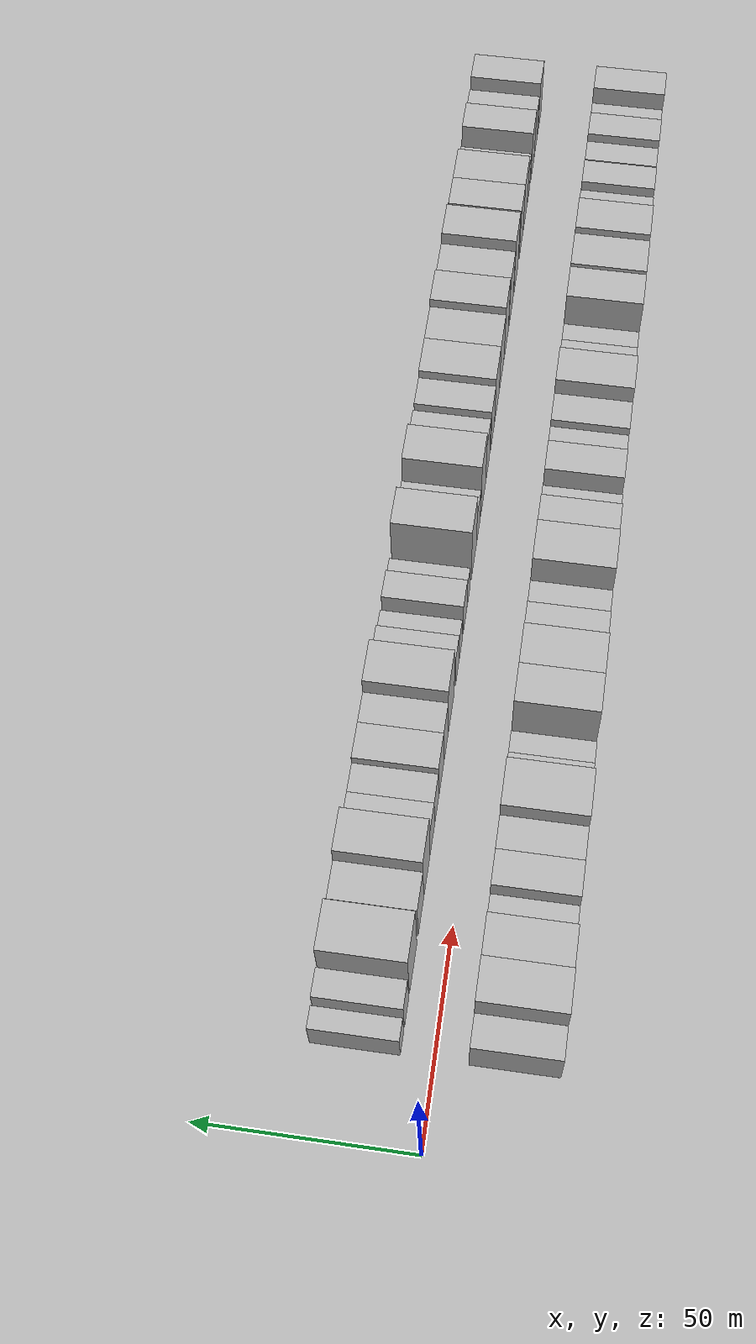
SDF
<?xml version="1.0" encoding="utf-8"?>

<sdf version="1.6">

   <world name="default">

      <gui fullscreen="0">

         <camera name="user_camera">

            <pose>-15 0 4.57585 0 0 0</pose>

            <view_controller>orbit</view_controller>

         </camera>

      </gui>

      <scene>

         <sky>

           <clouds>

             <speed>12</speed>

           </clouds>

         </sky>

         <ambient>0.4 0.4 0.4 1</ambient>

         <background>0.7 0.7 0.7 1</background>

         <shadows>1</shadows>

      </scene>

      <gravity>0 0 -9.8066</gravity>

      <magnetic_field>6e-06 2.3e-05 -4.2e-05</magnetic_field>

      <physics default="0" name="default_physics" type="ode">

         <ode>

            <solver>

               <type>quick</type>

               <iters>10</iters>

               <sor>1.0</sor>

               <use_dynamic_moi_rescaling>0</use_dynamic_moi_rescaling>

            </solver>

            <constraints>

               <cfm>0</cfm>

               <erp>0.2</erp>

               <contact_max_correcting_vel>100</contact_max_correcting_vel>

               <contact_surface_layer>0.001</contact_surface_layer>

            </constraints>

         </ode>

         <max_step_size>0.004</max_step_size>

         <real_time_factor>1</real_time_factor>

         <real_time_update_rate>250</real_time_update_rate>

      </physics>

      <light name="sun" type="directional">

         <cast_shadows>1</cast_shadows>

         <pose>0 0 10 0 0 0</pose>

         <diffuse>0.8 0.8 0.8 1</diffuse>

         <specular>0.2 0.2 0.2 1</specular>

         <attenuation>

            <range>1000</range>

            <constant>0.9</constant>

            <linear>0.01</linear>

            <quadratic>0.001</quadratic>

         </attenuation>

         <direction>-0.5 0.1 -0.9</direction>

      </light>

      <include>

         <name>ground_plane_1</name>

         <uri>model://HANNAS_ground_plane</uri>

         <pose>0 0 0  0 0 0</pose>

      </include>

      <include>

         <name>ground_plane_2</name>

         <uri>model://HANNAS_ground_plane</uri>

         <pose>100 0 0  0 0 0</pose>

      </include>

      <model name="building_1">

         <static>1</static>

         <pose frame="">22.5094 17.5000 0 0.000000 0.000000 1.570796</pose>

         <link name="link">

            <pose frame="">0 0 6.00 0 0 0</pose>

            <collision name="collision">

               <geometry>

                  <box>

                     <size>20.0000 5.0188 12.0000</size>

                  </box>

               </geometry>

               <max_contacts>10</max_contacts>

               <surface>

                  <contact>

                     <ode/>

                  </contact>

                  <bounce/>

                  <friction>

                     <torsional>

                        <ode/>

                     </torsional>

                     <ode/>

                  </friction>

               </surface>

            </collision>

            <visual name="visual">

               <cast_shadows>0</cast_shadows>

               <geometry>

                  <box>

                     <size>20.0000 5.0188 12.0000</size>

                  </box>

               </geometry>

               <material>

                  <script>

                     <uri>model://HANNAS_wall/materials/scripts</uri>

                     <uri>model://HANNAS_wall/materials/textures</uri>

                     <name>vrc/HANNAS_wall</name>

                  </script>

               </material>

            </visual>

            <self_collide>0</self_collide>

            <enable_wind>0</enable_wind>

            <kinematic>0</kinematic>

         </link>

      </model>

      <model name="building_2">

         <static>1</static>

         <pose frame="">29.2193 17.5000 0 0.000000 0.000000 1.570796</pose>

         <link name="link">

            <pose frame="">0 0 7.50 0 0 0</pose>

            <collision name="collision">

               <geometry>

                  <box>

                     <size>20.0000 6.4010 15.0000</size>

                  </box>

               </geometry>

               <max_contacts>10</max_contacts>

               <surface>

                  <contact>

                     <ode/>

                  </contact>

                  <bounce/>

                  <friction>

                     <torsional>

                        <ode/>

                     </torsional>

                     <ode/>

                  </friction>

               </surface>

            </collision>

            <visual name="visual">

               <cast_shadows>0</cast_shadows>

               <geometry>

                  <box>

                     <size>20.0000 6.4010 15.0000</size>

                  </box>

               </geometry>

               <material>

                  <script>

                     <uri>model://HANNAS_wall/materials/scripts</uri>

                     <uri>model://HANNAS_wall/materials/textures</uri>

                     <name>vrc/HANNAS_wall</name>

                  </script>

               </material>

            </visual>

            <self_collide>0</self_collide>

            <enable_wind>0</enable_wind>

            <kinematic>0</kinematic>

         </link>

      </model>

      <model name="building_3">

         <static>1</static>

         <pose frame="">39.0551 17.5000 0 0.000000 0.000000 1.570796</pose>

         <link name="link">

            <pose frame="">0 0 12.00 0 0 0</pose>

            <collision name="collision">

               <geometry>

                  <box>

                     <size>20.0000 11.2708 24.0000</size>

                  </box>

               </geometry>

               <max_contacts>10</max_contacts>

               <surface>

                  <contact>

                     <ode/>

                  </contact>

                  <bounce/>

                  <friction>

                     <torsional>

                        <ode/>

                     </torsional>

                     <ode/>

                  </friction>

               </surface>

            </collision>

            <visual name="visual">

               <cast_shadows>0</cast_shadows>

               <geometry>

                  <box>

                     <size>20.0000 11.2708 24.0000</size>

                  </box>

               </geometry>

               <material>

                  <script>

                     <uri>model://HANNAS_wall/materials/scripts</uri>

                     <uri>model://HANNAS_wall/materials/textures</uri>

                     <name>vrc/HANNAS_wall</name>

                  </script>

               </material>

            </visual>

            <self_collide>0</self_collide>

            <enable_wind>0</enable_wind>

            <kinematic>0</kinematic>

         </link>

      </model>

      <model name="building_4">

         <static>1</static>

         <pose frame="">51.0926 17.5000 0 0.000000 0.000000 1.570796</pose>

         <link name="link">

            <pose frame="">0 0 9.00 0 0 0</pose>

            <collision name="collision">

               <geometry>

                  <box>

                     <size>20.0000 8.8041 18.0000</size>

                  </box>

               </geometry>

               <max_contacts>10</max_contacts>

               <surface>

                  <contact>

                     <ode/>

                  </contact>

                  <bounce/>

                  <friction>

                     <torsional>

                        <ode/>

                     </torsional>

                     <ode/>

                  </friction>

               </surface>

            </collision>

            <visual name="visual">

               <cast_shadows>0</cast_shadows>

               <geometry>

                  <box>

                     <size>20.0000 8.8041 18.0000</size>

                  </box>

               </geometry>

               <material>

                  <script>

                     <uri>model://HANNAS_wall/materials/scripts</uri>

                     <uri>model://HANNAS_wall/materials/textures</uri>

                     <name>vrc/HANNAS_wall</name>

                  </script>

               </material>

            </visual>

            <self_collide>0</self_collide>

            <enable_wind>0</enable_wind>

            <kinematic>0</kinematic>

         </link>

      </model>

      <model name="building_5">

         <static>1</static>

         <pose frame="">60.5405 17.5000 0 0.000000 0.000000 1.570796</pose>

         <link name="link">

            <pose frame="">0 0 12.00 0 0 0</pose>

            <collision name="collision">

               <geometry>

                  <box>

                     <size>20.0000 10.0916 24.0000</size>

                  </box>

               </geometry>

               <max_contacts>10</max_contacts>

               <surface>

                  <contact>

                     <ode/>

                  </contact>

                  <bounce/>

                  <friction>

                     <torsional>

                        <ode/>

                     </torsional>

                     <ode/>

                  </friction>

               </surface>

            </collision>

            <visual name="visual">

               <cast_shadows>0</cast_shadows>

               <geometry>

                  <box>

                     <size>20.0000 10.0916 24.0000</size>

                  </box>

               </geometry>

               <material>

                  <script>

                     <uri>model://HANNAS_wall/materials/scripts</uri>

                     <uri>model://HANNAS_wall/materials/textures</uri>

                     <name>vrc/HANNAS_wall</name>

                  </script>

               </material>

            </visual>

            <self_collide>0</self_collide>

            <enable_wind>0</enable_wind>

            <kinematic>0</kinematic>

         </link>

      </model>

      <model name="building_6">

         <static>1</static>

         <pose frame="">69.2399 17.5000 0 0.000000 0.000000 1.570796</pose>

         <link name="link">

            <pose frame="">0 0 7.50 0 0 0</pose>

            <collision name="collision">

               <geometry>

                  <box>

                     <size>20.0000 7.3073 15.0000</size>

                  </box>

               </geometry>

               <max_contacts>10</max_contacts>

               <surface>

                  <contact>

                     <ode/>

                  </contact>

                  <bounce/>

                  <friction>

                     <torsional>

                        <ode/>

                     </torsional>

                     <ode/>

                  </friction>

               </surface>

            </collision>

            <visual name="visual">

               <cast_shadows>0</cast_shadows>

               <geometry>

                  <box>

                     <size>20.0000 7.3073 15.0000</size>

                  </box>

               </geometry>

               <material>

                  <script>

                     <uri>model://HANNAS_wall/materials/scripts</uri>

                     <uri>model://HANNAS_wall/materials/textures</uri>

                     <name>vrc/HANNAS_wall</name>

                  </script>

               </material>

            </visual>

            <self_collide>0</self_collide>

            <enable_wind>0</enable_wind>

            <kinematic>0</kinematic>

         </link>

      </model>

      <model name="building_7">

         <static>1</static>

         <pose frame="">76.4125 17.5000 0 0.000000 0.000000 1.570796</pose>

         <link name="link">

            <pose frame="">0 0 7.50 0 0 0</pose>

            <collision name="collision">

               <geometry>

                  <box>

                     <size>20.0000 7.0379 15.0000</size>

                  </box>

               </geometry>

               <max_contacts>10</max_contacts>

               <surface>

                  <contact>

                     <ode/>

                  </contact>

                  <bounce/>

                  <friction>

                     <torsional>

                        <ode/>

                     </torsional>

                     <ode/>

                  </friction>

               </surface>

            </collision>

            <visual name="visual">

               <cast_shadows>0</cast_shadows>

               <geometry>

                  <box>

                     <size>20.0000 7.0379 15.0000</size>

                  </box>

               </geometry>

               <material>

                  <script>

                     <uri>model://HANNAS_wall/materials/scripts</uri>

                     <uri>model://HANNAS_wall/materials/textures</uri>

                     <name>vrc/HANNAS_wall</name>

                  </script>

               </material>

            </visual>

            <self_collide>0</self_collide>

            <enable_wind>0</enable_wind>

            <kinematic>0</kinematic>

         </link>

      </model>

      <model name="building_8">

         <static>1</static>

         <pose frame="">84.3619 17.5000 0 0.000000 0.000000 1.570796</pose>

         <link name="link">

            <pose frame="">0 0 9.00 0 0 0</pose>

            <collision name="collision">

               <geometry>

                  <box>

                     <size>20.0000 8.8611 18.0000</size>

                  </box>

               </geometry>

               <max_contacts>10</max_contacts>

               <surface>

                  <contact>

                     <ode/>

                  </contact>

                  <bounce/>

                  <friction>

                     <torsional>

                        <ode/>

                     </torsional>

                     <ode/>

                  </friction>

               </surface>

            </collision>

            <visual name="visual">

               <cast_shadows>0</cast_shadows>

               <geometry>

                  <box>

                     <size>20.0000 8.8611 18.0000</size>

                  </box>

               </geometry>

               <material>

                  <script>

                     <uri>model://HANNAS_wall/materials/scripts</uri>

                     <uri>model://HANNAS_wall/materials/textures</uri>

                     <name>vrc/HANNAS_wall</name>

                  </script>

               </material>

            </visual>

            <self_collide>0</self_collide>

            <enable_wind>0</enable_wind>

            <kinematic>0</kinematic>

         </link>

      </model>

      <model name="building_9">

         <static>1</static>

         <pose frame="">92.5973 17.5000 0 0.000000 0.000000 1.570796</pose>

         <link name="link">

            <pose frame="">0 0 9.00 0 0 0</pose>

            <collision name="collision">

               <geometry>

                  <box>

                     <size>20.0000 7.6096 18.0000</size>

                  </box>

               </geometry>

               <max_contacts>10</max_contacts>

               <surface>

                  <contact>

                     <ode/>

                  </contact>

                  <bounce/>

                  <friction>

                     <torsional>

                        <ode/>

                     </torsional>

                     <ode/>

                  </friction>

               </surface>

            </collision>

            <visual name="visual">

               <cast_shadows>0</cast_shadows>

               <geometry>

                  <box>

                     <size>20.0000 7.6096 18.0000</size>

                  </box>

               </geometry>

               <material>

                  <script>

                     <uri>model://HANNAS_wall/materials/scripts</uri>

                     <uri>model://HANNAS_wall/materials/textures</uri>

                     <name>vrc/HANNAS_wall</name>

                  </script>

               </material>

            </visual>

            <self_collide>0</self_collide>

            <enable_wind>0</enable_wind>

            <kinematic>0</kinematic>

         </link>

      </model>

      <model name="building_10">

         <static>1</static>

         <pose frame="">101.7168 17.5000 0 0.000000 0.000000 1.570796</pose>

         <link name="link">

            <pose frame="">0 0 12.00 0 0 0</pose>

            <collision name="collision">

               <geometry>

                  <box>

                     <size>20.0000 10.6294 24.0000</size>

                  </box>

               </geometry>

               <max_contacts>10</max_contacts>

               <surface>

                  <contact>

                     <ode/>

                  </contact>

                  <bounce/>

                  <friction>

                     <torsional>

                        <ode/>

                     </torsional>

                     <ode/>

                  </friction>

               </surface>

            </collision>

            <visual name="visual">

               <cast_shadows>0</cast_shadows>

               <geometry>

                  <box>

                     <size>20.0000 10.6294 24.0000</size>

                  </box>

               </geometry>

               <material>

                  <script>

                     <uri>model://HANNAS_wall/materials/scripts</uri>

                     <uri>model://HANNAS_wall/materials/textures</uri>

                     <name>vrc/HANNAS_wall</name>

                  </script>

               </material>

            </visual>

            <self_collide>0</self_collide>

            <enable_wind>0</enable_wind>

            <kinematic>0</kinematic>

         </link>

      </model>

      <model name="building_11">

         <static>1</static>

         <pose frame="">112.2217 17.5000 0 0.000000 0.000000 1.570796</pose>

         <link name="link">

            <pose frame="">0 0 7.50 0 0 0</pose>

            <collision name="collision">

               <geometry>

                  <box>

                     <size>20.0000 6.3804 15.0000</size>

                  </box>

               </geometry>

               <max_contacts>10</max_contacts>

               <surface>

                  <contact>

                     <ode/>

                  </contact>

                  <bounce/>

                  <friction>

                     <torsional>

                        <ode/>

                     </torsional>

                     <ode/>

                  </friction>

               </surface>

            </collision>

            <visual name="visual">

               <cast_shadows>0</cast_shadows>

               <geometry>

                  <box>

                     <size>20.0000 6.3804 15.0000</size>

                  </box>

               </geometry>

               <material>

                  <script>

                     <uri>model://HANNAS_wall/materials/scripts</uri>

                     <uri>model://HANNAS_wall/materials/textures</uri>

                     <name>vrc/HANNAS_wall</name>

                  </script>

               </material>

            </visual>

            <self_collide>0</self_collide>

            <enable_wind>0</enable_wind>

            <kinematic>0</kinematic>

         </link>

      </model>

      <model name="building_12">

         <static>1</static>

         <pose frame="">118.2914 17.5000 0 0.000000 0.000000 1.570796</pose>

         <link name="link">

            <pose frame="">0 0 6.00 0 0 0</pose>

            <collision name="collision">

               <geometry>

                  <box>

                     <size>20.0000 5.7588 12.0000</size>

                  </box>

               </geometry>

               <max_contacts>10</max_contacts>

               <surface>

                  <contact>

                     <ode/>

                  </contact>

                  <bounce/>

                  <friction>

                     <torsional>

                        <ode/>

                     </torsional>

                     <ode/>

                  </friction>

               </surface>

            </collision>

            <visual name="visual">

               <cast_shadows>0</cast_shadows>

               <geometry>

                  <box>

                     <size>20.0000 5.7588 12.0000</size>

                  </box>

               </geometry>

               <material>

                  <script>

                     <uri>model://HANNAS_wall/materials/scripts</uri>

                     <uri>model://HANNAS_wall/materials/textures</uri>

                     <name>vrc/HANNAS_wall</name>

                  </script>

               </material>

            </visual>

            <self_collide>0</self_collide>

            <enable_wind>0</enable_wind>

            <kinematic>0</kinematic>

         </link>

      </model>

      <model name="building_13">

         <static>1</static>

         <pose frame="">126.8574 17.5000 0 0.000000 0.000000 1.570796</pose>

         <link name="link">

            <pose frame="">0 0 7.50 0 0 0</pose>

            <collision name="collision">

               <geometry>

                  <box>

                     <size>20.0000 7.3732 15.0000</size>

                  </box>

               </geometry>

               <max_contacts>10</max_contacts>

               <surface>

                  <contact>

                     <ode/>

                  </contact>

                  <bounce/>

                  <friction>

                     <torsional>

                        <ode/>

                     </torsional>

                     <ode/>

                  </friction>

               </surface>

            </collision>

            <visual name="visual">

               <cast_shadows>0</cast_shadows>

               <geometry>

                  <box>

                     <size>20.0000 7.3732 15.0000</size>

                  </box>

               </geometry>

               <material>

                  <script>

                     <uri>model://HANNAS_wall/materials/scripts</uri>

                     <uri>model://HANNAS_wall/materials/textures</uri>

                     <name>vrc/HANNAS_wall</name>

                  </script>

               </material>

            </visual>

            <self_collide>0</self_collide>

            <enable_wind>0</enable_wind>

            <kinematic>0</kinematic>

         </link>

      </model>

      <model name="building_14">

         <static>1</static>

         <pose frame="">133.0565 17.5000 0 0.000000 0.000000 1.570796</pose>

         <link name="link">

            <pose frame="">0 0 6.00 0 0 0</pose>

            <collision name="collision">

               <geometry>

                  <box>

                     <size>20.0000 5.0249 12.0000</size>

                  </box>

               </geometry>

               <max_contacts>10</max_contacts>

               <surface>

                  <contact>

                     <ode/>

                  </contact>

                  <bounce/>

                  <friction>

                     <torsional>

                        <ode/>

                     </torsional>

                     <ode/>

                  </friction>

               </surface>

            </collision>

            <visual name="visual">

               <cast_shadows>0</cast_shadows>

               <geometry>

                  <box>

                     <size>20.0000 5.0249 12.0000</size>

                  </box>

               </geometry>

               <material>

                  <script>

                     <uri>model://HANNAS_wall/materials/scripts</uri>

                     <uri>model://HANNAS_wall/materials/textures</uri>

                     <name>vrc/HANNAS_wall</name>

                  </script>

               </material>

            </visual>

            <self_collide>0</self_collide>

            <enable_wind>0</enable_wind>

            <kinematic>0</kinematic>

         </link>

      </model>

      <model name="building_15">

         <static>1</static>

         <pose frame="">143.6724 17.5000 0 0.000000 0.000000 1.570796</pose>

         <link name="link">

            <pose frame="">0 0 12.00 0 0 0</pose>

            <collision name="collision">

               <geometry>

                  <box>

                     <size>20.0000 10.2068 24.0000</size>

                  </box>

               </geometry>

               <max_contacts>10</max_contacts>

               <surface>

                  <contact>

                     <ode/>

                  </contact>

                  <bounce/>

                  <friction>

                     <torsional>

                        <ode/>

                     </torsional>

                     <ode/>

                  </friction>

               </surface>

            </collision>

            <visual name="visual">

               <cast_shadows>0</cast_shadows>

               <geometry>

                  <box>

                     <size>20.0000 10.2068 24.0000</size>

                  </box>

               </geometry>

               <material>

                  <script>

                     <uri>model://HANNAS_wall/materials/scripts</uri>

                     <uri>model://HANNAS_wall/materials/textures</uri>

                     <name>vrc/HANNAS_wall</name>

                  </script>

               </material>

            </visual>

            <self_collide>0</self_collide>

            <enable_wind>0</enable_wind>

            <kinematic>0</kinematic>

         </link>

      </model>

      <model name="building_16">

         <static>1</static>

         <pose frame="">152.4874 17.5000 0 0.000000 0.000000 1.570796</pose>

         <link name="link">

            <pose frame="">0 0 7.50 0 0 0</pose>

            <collision name="collision">

               <geometry>

                  <box>

                     <size>20.0000 7.4232 15.0000</size>

                  </box>

               </geometry>

               <max_contacts>10</max_contacts>

               <surface>

                  <contact>

                     <ode/>

                  </contact>

                  <bounce/>

                  <friction>

                     <torsional>

                        <ode/>

                     </torsional>

                     <ode/>

                  </friction>

               </surface>

            </collision>

            <visual name="visual">

               <cast_shadows>0</cast_shadows>

               <geometry>

                  <box>

                     <size>20.0000 7.4232 15.0000</size>

                  </box>

               </geometry>

               <material>

                  <script>

                     <uri>model://HANNAS_wall/materials/scripts</uri>

                     <uri>model://HANNAS_wall/materials/textures</uri>

                     <name>vrc/HANNAS_wall</name>

                  </script>

               </material>

            </visual>

            <self_collide>0</self_collide>

            <enable_wind>0</enable_wind>

            <kinematic>0</kinematic>

         </link>

      </model>

      <model name="building_17">

         <static>1</static>

         <pose frame="">162.2632 17.5000 0 0.000000 0.000000 1.570796</pose>

         <link name="link">

            <pose frame="">0 0 12.00 0 0 0</pose>

            <collision name="collision">

               <geometry>

                  <box>

                     <size>20.0000 10.1284 24.0000</size>

                  </box>

               </geometry>

               <max_contacts>10</max_contacts>

               <surface>

                  <contact>

                     <ode/>

                  </contact>

                  <bounce/>

                  <friction>

                     <torsional>

                        <ode/>

                     </torsional>

                     <ode/>

                  </friction>

               </surface>

            </collision>

            <visual name="visual">

               <cast_shadows>0</cast_shadows>

               <geometry>

                  <box>

                     <size>20.0000 10.1284 24.0000</size>

                  </box>

               </geometry>

               <material>

                  <script>

                     <uri>model://HANNAS_wall/materials/scripts</uri>

                     <uri>model://HANNAS_wall/materials/textures</uri>

                     <name>vrc/HANNAS_wall</name>

                  </script>

               </material>

            </visual>

            <self_collide>0</self_collide>

            <enable_wind>0</enable_wind>

            <kinematic>0</kinematic>

         </link>

      </model>

      <model name="building_18">

         <static>1</static>

         <pose frame="">171.4944 17.5000 0 0.000000 0.000000 1.570796</pose>

         <link name="link">

            <pose frame="">0 0 9.00 0 0 0</pose>

            <collision name="collision">

               <geometry>

                  <box>

                     <size>20.0000 8.3341 18.0000</size>

                  </box>

               </geometry>

               <max_contacts>10</max_contacts>

               <surface>

                  <contact>

                     <ode/>

                  </contact>

                  <bounce/>

                  <friction>

                     <torsional>

                        <ode/>

                     </torsional>

                     <ode/>

                  </friction>

               </surface>

            </collision>

            <visual name="visual">

               <cast_shadows>0</cast_shadows>

               <geometry>

                  <box>

                     <size>20.0000 8.3341 18.0000</size>

                  </box>

               </geometry>

               <material>

                  <script>

                     <uri>model://HANNAS_wall/materials/scripts</uri>

                     <uri>model://HANNAS_wall/materials/textures</uri>

                     <name>vrc/HANNAS_wall</name>

                  </script>

               </material>

            </visual>

            <self_collide>0</self_collide>

            <enable_wind>0</enable_wind>

            <kinematic>0</kinematic>

         </link>

      </model>

      <model name="building_19">

         <static>1</static>

         <pose frame="">181.7442 17.5000 0 0.000000 0.000000 1.570796</pose>

         <link name="link">

            <pose frame="">0 0 9.00 0 0 0</pose>

            <collision name="collision">

               <geometry>

                  <box>

                     <size>20.0000 8.1655 18.0000</size>

                  </box>

               </geometry>

               <max_contacts>10</max_contacts>

               <surface>

                  <contact>

                     <ode/>

                  </contact>

                  <bounce/>

                  <friction>

                     <torsional>

                        <ode/>

                     </torsional>

                     <ode/>

                  </friction>

               </surface>

            </collision>

            <visual name="visual">

               <cast_shadows>0</cast_shadows>

               <geometry>

                  <box>

                     <size>20.0000 8.1655 18.0000</size>

                  </box>

               </geometry>

               <material>

                  <script>

                     <uri>model://HANNAS_wall/materials/scripts</uri>

                     <uri>model://HANNAS_wall/materials/textures</uri>

                     <name>vrc/HANNAS_wall</name>

                  </script>

               </material>

            </visual>

            <self_collide>0</self_collide>

            <enable_wind>0</enable_wind>

            <kinematic>0</kinematic>

         </link>

      </model>

      <model name="building_20">

         <static>1</static>

         <pose frame="">191.0521 17.5000 0 0.000000 0.000000 1.570796</pose>

         <link name="link">

            <pose frame="">0 0 10.50 0 0 0</pose>

            <collision name="collision">

               <geometry>

                  <box>

                     <size>20.0000 10.4504 21.0000</size>

                  </box>

               </geometry>

               <max_contacts>10</max_contacts>

               <surface>

                  <contact>

                     <ode/>

                  </contact>

                  <bounce/>

                  <friction>

                     <torsional>

                        <ode/>

                     </torsional>

                     <ode/>

                  </friction>

               </surface>

            </collision>

            <visual name="visual">

               <cast_shadows>0</cast_shadows>

               <geometry>

                  <box>

                     <size>20.0000 10.4504 21.0000</size>

                  </box>

               </geometry>

               <material>

                  <script>

                     <uri>model://HANNAS_wall/materials/scripts</uri>

                     <uri>model://HANNAS_wall/materials/textures</uri>

                     <name>vrc/HANNAS_wall</name>

                  </script>

               </material>

            </visual>

            <self_collide>0</self_collide>

            <enable_wind>0</enable_wind>

            <kinematic>0</kinematic>

         </link>

      </model>

      <model name="building_21">

         <static>1</static>

         <pose frame="">201.3887 17.5000 0 0.000000 0.000000 1.570796</pose>

         <link name="link">

            <pose frame="">0 0 10.50 0 0 0</pose>

            <collision name="collision">

               <geometry>

                  <box>

                     <size>20.0000 10.2229 21.0000</size>

                  </box>

               </geometry>

               <max_contacts>10</max_contacts>

               <surface>

                  <contact>

                     <ode/>

                  </contact>

                  <bounce/>

                  <friction>

                     <torsional>

                        <ode/>

                     </torsional>

                     <ode/>

                  </friction>

               </surface>

            </collision>

            <visual name="visual">

               <cast_shadows>0</cast_shadows>

               <geometry>

                  <box>

                     <size>20.0000 10.2229 21.0000</size>

                  </box>

               </geometry>

               <material>

                  <script>

                     <uri>model://HANNAS_wall/materials/scripts</uri>

                     <uri>model://HANNAS_wall/materials/textures</uri>

                     <name>vrc/HANNAS_wall</name>

                  </script>

               </material>

            </visual>

            <self_collide>0</self_collide>

            <enable_wind>0</enable_wind>

            <kinematic>0</kinematic>

         </link>

      </model>

      <model name="building_22">

         <static>1</static>

         <pose frame="">211.4315 17.5000 0 0.000000 0.000000 1.570796</pose>

         <link name="link">

            <pose frame="">0 0 12.00 0 0 0</pose>

            <collision name="collision">

               <geometry>

                  <box>

                     <size>20.0000 9.8627 24.0000</size>

                  </box>

               </geometry>

               <max_contacts>10</max_contacts>

               <surface>

                  <contact>

                     <ode/>

                  </contact>

                  <bounce/>

                  <friction>

                     <torsional>

                        <ode/>

                     </torsional>

                     <ode/>

                  </friction>

               </surface>

            </collision>

            <visual name="visual">

               <cast_shadows>0</cast_shadows>

               <geometry>

                  <box>

                     <size>20.0000 9.8627 24.0000</size>

                  </box>

               </geometry>

               <material>

                  <script>

                     <uri>model://HANNAS_wall/materials/scripts</uri>

                     <uri>model://HANNAS_wall/materials/textures</uri>

                     <name>vrc/HANNAS_wall</name>

                  </script>

               </material>

            </visual>

            <self_collide>0</self_collide>

            <enable_wind>0</enable_wind>

            <kinematic>0</kinematic>

         </link>

      </model>

      <model name="building_23">

         <static>1</static>

         <pose frame="">222.5453 17.5000 0 0.000000 0.000000 1.570796</pose>

         <link name="link">

            <pose frame="">0 0 10.50 0 0 0</pose>

            <collision name="collision">

               <geometry>

                  <box>

                     <size>20.0000 10.3650 21.0000</size>

                  </box>

               </geometry>

               <max_contacts>10</max_contacts>

               <surface>

                  <contact>

                     <ode/>

                  </contact>

                  <bounce/>

                  <friction>

                     <torsional>

                        <ode/>

                     </torsional>

                     <ode/>

                  </friction>

               </surface>

            </collision>

            <visual name="visual">

               <cast_shadows>0</cast_shadows>

               <geometry>

                  <box>

                     <size>20.0000 10.3650 21.0000</size>

                  </box>

               </geometry>

               <material>

                  <script>

                     <uri>model://HANNAS_wall/materials/scripts</uri>

                     <uri>model://HANNAS_wall/materials/textures</uri>

                     <name>vrc/HANNAS_wall</name>

                  </script>

               </material>

            </visual>

            <self_collide>0</self_collide>

            <enable_wind>0</enable_wind>

            <kinematic>0</kinematic>

         </link>

      </model>

      <model name="building_24">

         <static>1</static>

         <pose frame="">233.7784 17.5000 0 0.000000 0.000000 1.570796</pose>

         <link name="link">

            <pose frame="">0 0 12.00 0 0 0</pose>

            <collision name="collision">

               <geometry>

                  <box>

                     <size>20.0000 10.1011 24.0000</size>

                  </box>

               </geometry>

               <max_contacts>10</max_contacts>

               <surface>

                  <contact>

                     <ode/>

                  </contact>

                  <bounce/>

                  <friction>

                     <torsional>

                        <ode/>

                     </torsional>

                     <ode/>

                  </friction>

               </surface>

            </collision>

            <visual name="visual">

               <cast_shadows>0</cast_shadows>

               <geometry>

                  <box>

                     <size>20.0000 10.1011 24.0000</size>

                  </box>

               </geometry>

               <material>

                  <script>

                     <uri>model://HANNAS_wall/materials/scripts</uri>

                     <uri>model://HANNAS_wall/materials/textures</uri>

                     <name>vrc/HANNAS_wall</name>

                  </script>

               </material>

            </visual>

            <self_collide>0</self_collide>

            <enable_wind>0</enable_wind>

            <kinematic>0</kinematic>

         </link>

      </model>

      <model name="building_25">

         <static>1</static>

         <pose frame="">246.5001 17.5000 0 0.000000 0.000000 1.570796</pose>

         <link name="link">

            <pose frame="">0 0 10.50 0 0 0</pose>

            <collision name="collision">

               <geometry>

                  <box>

                     <size>20.0000 9.3423 21.0000</size>

                  </box>

               </geometry>

               <max_contacts>10</max_contacts>

               <surface>

                  <contact>

                     <ode/>

                  </contact>

                  <bounce/>

                  <friction>

                     <torsional>

                        <ode/>

                     </torsional>

                     <ode/>

                  </friction>

               </surface>

            </collision>

            <visual name="visual">

               <cast_shadows>0</cast_shadows>

               <geometry>

                  <box>

                     <size>20.0000 9.3423 21.0000</size>

                  </box>

               </geometry>

               <material>

                  <script>

                     <uri>model://HANNAS_wall/materials/scripts</uri>

                     <uri>model://HANNAS_wall/materials/textures</uri>

                     <name>vrc/HANNAS_wall</name>

                  </script>

               </material>

            </visual>

            <self_collide>0</self_collide>

            <enable_wind>0</enable_wind>

            <kinematic>0</kinematic>

         </link>

      </model>

      <model name="building_26">

         <static>1</static>

         <pose frame="">256.3676 17.5000 0 0.000000 0.000000 1.570796</pose>

         <link name="link">

            <pose frame="">0 0 10.50 0 0 0</pose>

            <collision name="collision">

               <geometry>

                  <box>

                     <size>20.0000 10.3927 21.0000</size>

                  </box>

               </geometry>

               <max_contacts>10</max_contacts>

               <surface>

                  <contact>

                     <ode/>

                  </contact>

                  <bounce/>

                  <friction>

                     <torsional>

                        <ode/>

                     </torsional>

                     <ode/>

                  </friction>

               </surface>

            </collision>

            <visual name="visual">

               <cast_shadows>0</cast_shadows>

               <geometry>

                  <box>

                     <size>20.0000 10.3927 21.0000</size>

                  </box>

               </geometry>

               <material>

                  <script>

                     <uri>model://HANNAS_wall/materials/scripts</uri>

                     <uri>model://HANNAS_wall/materials/textures</uri>

                     <name>vrc/HANNAS_wall</name>

                  </script>

               </material>

            </visual>

            <self_collide>0</self_collide>

            <enable_wind>0</enable_wind>

            <kinematic>0</kinematic>

         </link>

      </model>

      <model name="building_27">

         <static>1</static>

         <pose frame="">264.7600 17.5000 0 0.000000 0.000000 1.570796</pose>

         <link name="link">

            <pose frame="">0 0 7.50 0 0 0</pose>

            <collision name="collision">

               <geometry>

                  <box>

                     <size>20.0000 6.3921 15.0000</size>

                  </box>

               </geometry>

               <max_contacts>10</max_contacts>

               <surface>

                  <contact>

                     <ode/>

                  </contact>

                  <bounce/>

                  <friction>

                     <torsional>

                        <ode/>

                     </torsional>

                     <ode/>

                  </friction>

               </surface>

            </collision>

            <visual name="visual">

               <cast_shadows>0</cast_shadows>

               <geometry>

                  <box>

                     <size>20.0000 6.3921 15.0000</size>

                  </box>

               </geometry>

               <material>

                  <script>

                     <uri>model://HANNAS_wall/materials/scripts</uri>

                     <uri>model://HANNAS_wall/materials/textures</uri>

                     <name>vrc/HANNAS_wall</name>

                  </script>

               </material>

            </visual>

            <self_collide>0</self_collide>

            <enable_wind>0</enable_wind>

            <kinematic>0</kinematic>

         </link>

      </model>

      <model name="building_28">

         <static>1</static>

         <pose frame="">274.4199 17.5000 0 0.000000 0.000000 1.570796</pose>

         <link name="link">

            <pose frame="">0 0 10.50 0 0 0</pose>

            <collision name="collision">

               <geometry>

                  <box>

                     <size>20.0000 8.9277 21.0000</size>

                  </box>

               </geometry>

               <max_contacts>10</max_contacts>

               <surface>

                  <contact>

                     <ode/>

                  </contact>

                  <bounce/>

                  <friction>

                     <torsional>

                        <ode/>

                     </torsional>

                     <ode/>

                  </friction>

               </surface>

            </collision>

            <visual name="visual">

               <cast_shadows>0</cast_shadows>

               <geometry>

                  <box>

                     <size>20.0000 8.9277 21.0000</size>

                  </box>

               </geometry>

               <material>

                  <script>

                     <uri>model://HANNAS_wall/materials/scripts</uri>

                     <uri>model://HANNAS_wall/materials/textures</uri>

                     <name>vrc/HANNAS_wall</name>

                  </script>

               </material>

            </visual>

            <self_collide>0</self_collide>

            <enable_wind>0</enable_wind>

            <kinematic>0</kinematic>

         </link>

      </model>

      <model name="building_29">

         <static>1</static>

         <pose frame="">282.9135 17.5000 0 0.000000 0.000000 1.570796</pose>

         <link name="link">

            <pose frame="">0 0 9.00 0 0 0</pose>

            <collision name="collision">

               <geometry>

                  <box>

                     <size>20.0000 8.0595 18.0000</size>

                  </box>

               </geometry>

               <max_contacts>10</max_contacts>

               <surface>

                  <contact>

                     <ode/>

                  </contact>

                  <bounce/>

                  <friction>

                     <torsional>

                        <ode/>

                     </torsional>

                     <ode/>

                  </friction>

               </surface>

            </collision>

            <visual name="visual">

               <cast_shadows>0</cast_shadows>

               <geometry>

                  <box>

                     <size>20.0000 8.0595 18.0000</size>

                  </box>

               </geometry>

               <material>

                  <script>

                     <uri>model://HANNAS_wall/materials/scripts</uri>

                     <uri>model://HANNAS_wall/materials/textures</uri>

                     <name>vrc/HANNAS_wall</name>

                  </script>

               </material>

            </visual>

            <self_collide>0</self_collide>

            <enable_wind>0</enable_wind>

            <kinematic>0</kinematic>

         </link>

      </model>

      <model name="building_30">

         <static>1</static>

         <pose frame="">293.4200 17.5000 0 0.000000 0.000000 1.570796</pose>

         <link name="link">

            <pose frame="">0 0 10.50 0 0 0</pose>

            <collision name="collision">

               <geometry>

                  <box>

                     <size>20.0000 8.9536 21.0000</size>

                  </box>

               </geometry>

               <max_contacts>10</max_contacts>

               <surface>

                  <contact>

                     <ode/>

                  </contact>

                  <bounce/>

                  <friction>

                     <torsional>

                        <ode/>

                     </torsional>

                     <ode/>

                  </friction>

               </surface>

            </collision>

            <visual name="visual">

               <cast_shadows>0</cast_shadows>

               <geometry>

                  <box>

                     <size>20.0000 8.9536 21.0000</size>

                  </box>

               </geometry>

               <material>

                  <script>

                     <uri>model://HANNAS_wall/materials/scripts</uri>

                     <uri>model://HANNAS_wall/materials/textures</uri>

                     <name>vrc/HANNAS_wall</name>

                  </script>

               </material>

            </visual>

            <self_collide>0</self_collide>

            <enable_wind>0</enable_wind>

            <kinematic>0</kinematic>

         </link>

      </model>

      <model name="building_31">

         <static>1</static>

         <pose frame="">23.7137 -17.5000 0 0.000000 0.000000 1.570796</pose>

         <link name="link">

            <pose frame="">0 0 7.50 0 0 0</pose>

            <collision name="collision">

               <geometry>

                  <box>

                     <size>20.0000 7.4273 15.0000</size>

                  </box>

               </geometry>

               <max_contacts>10</max_contacts>

               <surface>

                  <contact>

                     <ode/>

                  </contact>

                  <bounce/>

                  <friction>

                     <torsional>

                        <ode/>

                     </torsional>

                     <ode/>

                  </friction>

               </surface>

            </collision>

            <visual name="visual">

               <cast_shadows>0</cast_shadows>

               <geometry>

                  <box>

                     <size>20.0000 7.4273 15.0000</size>

                  </box>

               </geometry>

               <material>

                  <script>

                     <uri>model://HANNAS_wall/materials/scripts</uri>

                     <uri>model://HANNAS_wall/materials/textures</uri>

                     <name>vrc/HANNAS_wall</name>

                  </script>

               </material>

            </visual>

            <self_collide>0</self_collide>

            <enable_wind>0</enable_wind>

            <kinematic>0</kinematic>

         </link>

      </model>

      <model name="building_32">

         <static>1</static>

         <pose frame="">32.3466 -17.5000 0 0.000000 0.000000 1.570796</pose>

         <link name="link">

            <pose frame="">0 0 12.00 0 0 0</pose>

            <collision name="collision">

               <geometry>

                  <box>

                     <size>20.0000 9.8386 24.0000</size>

                  </box>

               </geometry>

               <max_contacts>10</max_contacts>

               <surface>

                  <contact>

                     <ode/>

                  </contact>

                  <bounce/>

                  <friction>

                     <torsional>

                        <ode/>

                     </torsional>

                     <ode/>

                  </friction>

               </surface>

            </collision>

            <visual name="visual">

               <cast_shadows>0</cast_shadows>

               <geometry>

                  <box>

                     <size>20.0000 9.8386 24.0000</size>

                  </box>

               </geometry>

               <material>

                  <script>

                     <uri>model://HANNAS_wall/materials/scripts</uri>

                     <uri>model://HANNAS_wall/materials/textures</uri>

                     <name>vrc/HANNAS_wall</name>

                  </script>

               </material>

            </visual>

            <self_collide>0</self_collide>

            <enable_wind>0</enable_wind>

            <kinematic>0</kinematic>

         </link>

      </model>

      <model name="building_33">

         <static>1</static>

         <pose frame="">42.4667 -17.5000 0 0.000000 0.000000 1.570796</pose>

         <link name="link">

            <pose frame="">0 0 10.50 0 0 0</pose>

            <collision name="collision">

               <geometry>

                  <box>

                     <size>20.0000 10.4016 21.0000</size>

                  </box>

               </geometry>

               <max_contacts>10</max_contacts>

               <surface>

                  <contact>

                     <ode/>

                  </contact>

                  <bounce/>

                  <friction>

                     <torsional>

                        <ode/>

                     </torsional>

                     <ode/>

                  </friction>

               </surface>

            </collision>

            <visual name="visual">

               <cast_shadows>0</cast_shadows>

               <geometry>

                  <box>

                     <size>20.0000 10.4016 21.0000</size>

                  </box>

               </geometry>

               <material>

                  <script>

                     <uri>model://HANNAS_wall/materials/scripts</uri>

                     <uri>model://HANNAS_wall/materials/textures</uri>

                     <name>vrc/HANNAS_wall</name>

                  </script>

               </material>

            </visual>

            <self_collide>0</self_collide>

            <enable_wind>0</enable_wind>

            <kinematic>0</kinematic>

         </link>

      </model>

      <model name="building_34">

         <static>1</static>

         <pose frame="">52.2176 -17.5000 0 0.000000 0.000000 1.570796</pose>

         <link name="link">

            <pose frame="">0 0 6.00 0 0 0</pose>

            <collision name="collision">

               <geometry>

                  <box>

                     <size>20.0000 5.1002 12.0000</size>

                  </box>

               </geometry>

               <max_contacts>10</max_contacts>

               <surface>

                  <contact>

                     <ode/>

                  </contact>

                  <bounce/>

                  <friction>

                     <torsional>

                        <ode/>

                     </torsional>

                     <ode/>

                  </friction>

               </surface>

            </collision>

            <visual name="visual">

               <cast_shadows>0</cast_shadows>

               <geometry>

                  <box>

                     <size>20.0000 5.1002 12.0000</size>

                  </box>

               </geometry>

               <material>

                  <script>

                     <uri>model://HANNAS_wall/materials/scripts</uri>

                     <uri>model://HANNAS_wall/materials/textures</uri>

                     <name>vrc/HANNAS_wall</name>

                  </script>

               </material>

            </visual>

            <self_collide>0</self_collide>

            <enable_wind>0</enable_wind>

            <kinematic>0</kinematic>

         </link>

      </model>

      <model name="building_35">

         <static>1</static>

         <pose frame="">58.9409 -17.5000 0 0.000000 0.000000 1.570796</pose>

         <link name="link">

            <pose frame="">0 0 9.00 0 0 0</pose>

            <collision name="collision">

               <geometry>

                  <box>

                     <size>20.0000 8.3465 18.0000</size>

                  </box>

               </geometry>

               <max_contacts>10</max_contacts>

               <surface>

                  <contact>

                     <ode/>

                  </contact>

                  <bounce/>

                  <friction>

                     <torsional>

                        <ode/>

                     </torsional>

                     <ode/>

                  </friction>

               </surface>

            </collision>

            <visual name="visual">

               <cast_shadows>0</cast_shadows>

               <geometry>

                  <box>

                     <size>20.0000 8.3465 18.0000</size>

                  </box>

               </geometry>

               <material>

                  <script>

                     <uri>model://HANNAS_wall/materials/scripts</uri>

                     <uri>model://HANNAS_wall/materials/textures</uri>

                     <name>vrc/HANNAS_wall</name>

                  </script>

               </material>

            </visual>

            <self_collide>0</self_collide>

            <enable_wind>0</enable_wind>

            <kinematic>0</kinematic>

         </link>

      </model>

      <model name="building_36">

         <static>1</static>

         <pose frame="">67.0634 -17.5000 0 0.000000 0.000000 1.570796</pose>

         <link name="link">

            <pose frame="">0 0 9.00 0 0 0</pose>

            <collision name="collision">

               <geometry>

                  <box>

                     <size>20.0000 7.8986 18.0000</size>

                  </box>

               </geometry>

               <max_contacts>10</max_contacts>

               <surface>

                  <contact>

                     <ode/>

                  </contact>

                  <bounce/>

                  <friction>

                     <torsional>

                        <ode/>

                     </torsional>

                     <ode/>

                  </friction>

               </surface>

            </collision>

            <visual name="visual">

               <cast_shadows>0</cast_shadows>

               <geometry>

                  <box>

                     <size>20.0000 7.8986 18.0000</size>

                  </box>

               </geometry>

               <material>

                  <script>

                     <uri>model://HANNAS_wall/materials/scripts</uri>

                     <uri>model://HANNAS_wall/materials/textures</uri>

                     <name>vrc/HANNAS_wall</name>

                  </script>

               </material>

            </visual>

            <self_collide>0</self_collide>

            <enable_wind>0</enable_wind>

            <kinematic>0</kinematic>

         </link>

      </model>

      <model name="building_37">

         <static>1</static>

         <pose frame="">76.7283 -17.5000 0 0.000000 0.000000 1.570796</pose>

         <link name="link">

            <pose frame="">0 0 12.00 0 0 0</pose>

            <collision name="collision">

               <geometry>

                  <box>

                     <size>20.0000 11.4311 24.0000</size>

                  </box>

               </geometry>

               <max_contacts>10</max_contacts>

               <surface>

                  <contact>

                     <ode/>

                  </contact>

                  <bounce/>

                  <friction>

                     <torsional>

                        <ode/>

                     </torsional>

                     <ode/>

                  </friction>

               </surface>

            </collision>

            <visual name="visual">

               <cast_shadows>0</cast_shadows>

               <geometry>

                  <box>

                     <size>20.0000 11.4311 24.0000</size>

                  </box>

               </geometry>

               <material>

                  <script>

                     <uri>model://HANNAS_wall/materials/scripts</uri>

                     <uri>model://HANNAS_wall/materials/textures</uri>

                     <name>vrc/HANNAS_wall</name>

                  </script>

               </material>

            </visual>

            <self_collide>0</self_collide>

            <enable_wind>0</enable_wind>

            <kinematic>0</kinematic>

         </link>

      </model>

      <model name="building_38">

         <static>1</static>

         <pose frame="">86.1244 -17.5000 0 0.000000 0.000000 1.570796</pose>

         <link name="link">

            <pose frame="">0 0 6.00 0 0 0</pose>

            <collision name="collision">

               <geometry>

                  <box>

                     <size>20.0000 5.3612 12.0000</size>

                  </box>

               </geometry>

               <max_contacts>10</max_contacts>

               <surface>

                  <contact>

                     <ode/>

                  </contact>

                  <bounce/>

                  <friction>

                     <torsional>

                        <ode/>

                     </torsional>

                     <ode/>

                  </friction>

               </surface>

            </collision>

            <visual name="visual">

               <cast_shadows>0</cast_shadows>

               <geometry>

                  <box>

                     <size>20.0000 5.3612 12.0000</size>

                  </box>

               </geometry>

               <material>

                  <script>

                     <uri>model://HANNAS_wall/materials/scripts</uri>

                     <uri>model://HANNAS_wall/materials/textures</uri>

                     <name>vrc/HANNAS_wall</name>

                  </script>

               </material>

            </visual>

            <self_collide>0</self_collide>

            <enable_wind>0</enable_wind>

            <kinematic>0</kinematic>

         </link>

      </model>

      <model name="building_39">

         <static>1</static>

         <pose frame="">91.4952 -17.5000 0 0.000000 0.000000 1.570796</pose>

         <link name="link">

            <pose frame="">0 0 6.00 0 0 0</pose>

            <collision name="collision">

               <geometry>

                  <box>

                     <size>20.0000 5.3804 12.0000</size>

                  </box>

               </geometry>

               <max_contacts>10</max_contacts>

               <surface>

                  <contact>

                     <ode/>

                  </contact>

                  <bounce/>

                  <friction>

                     <torsional>

                        <ode/>

                     </torsional>

                     <ode/>

                  </friction>

               </surface>

            </collision>

            <visual name="visual">

               <cast_shadows>0</cast_shadows>

               <geometry>

                  <box>

                     <size>20.0000 5.3804 12.0000</size>

                  </box>

               </geometry>

               <material>

                  <script>

                     <uri>model://HANNAS_wall/materials/scripts</uri>

                     <uri>model://HANNAS_wall/materials/textures</uri>

                     <name>vrc/HANNAS_wall</name>

                  </script>

               </material>

            </visual>

            <self_collide>0</self_collide>

            <enable_wind>0</enable_wind>

            <kinematic>0</kinematic>

         </link>

      </model>

      <model name="building_40">

         <static>1</static>

         <pose frame="">101.0883 -17.5000 0 0.000000 0.000000 1.570796</pose>

         <link name="link">

            <pose frame="">0 0 12.00 0 0 0</pose>

            <collision name="collision">

               <geometry>

                  <box>

                     <size>20.0000 9.8059 24.0000</size>

                  </box>

               </geometry>

               <max_contacts>10</max_contacts>

               <surface>

                  <contact>

                     <ode/>

                  </contact>

                  <bounce/>

                  <friction>

                     <torsional>

                        <ode/>

                     </torsional>

                     <ode/>

                  </friction>

               </surface>

            </collision>

            <visual name="visual">

               <cast_shadows>0</cast_shadows>

               <geometry>

                  <box>

                     <size>20.0000 9.8059 24.0000</size>

                  </box>

               </geometry>

               <material>

                  <script>

                     <uri>model://HANNAS_wall/materials/scripts</uri>

                     <uri>model://HANNAS_wall/materials/textures</uri>

                     <name>vrc/HANNAS_wall</name>

                  </script>

               </material>

            </visual>

            <self_collide>0</self_collide>

            <enable_wind>0</enable_wind>

            <kinematic>0</kinematic>

         </link>

      </model>

      <model name="building_41">

         <static>1</static>

         <pose frame="">111.1877 -17.5000 0 0.000000 0.000000 1.570796</pose>

         <link name="link">

            <pose frame="">0 0 12.00 0 0 0</pose>

            <collision name="collision">

               <geometry>

                  <box>

                     <size>20.0000 10.3929 24.0000</size>

                  </box>

               </geometry>

               <max_contacts>10</max_contacts>

               <surface>

                  <contact>

                     <ode/>

                  </contact>

                  <bounce/>

                  <friction>

                     <torsional>

                        <ode/>

                     </torsional>

                     <ode/>

                  </friction>

               </surface>

            </collision>

            <visual name="visual">

               <cast_shadows>0</cast_shadows>

               <geometry>

                  <box>

                     <size>20.0000 10.3929 24.0000</size>

                  </box>

               </geometry>

               <material>

                  <script>

                     <uri>model://HANNAS_wall/materials/scripts</uri>

                     <uri>model://HANNAS_wall/materials/textures</uri>

                     <name>vrc/HANNAS_wall</name>

                  </script>

               </material>

            </visual>

            <self_collide>0</self_collide>

            <enable_wind>0</enable_wind>

            <kinematic>0</kinematic>

         </link>

      </model>

      <model name="building_42">

         <static>1</static>

         <pose frame="">120.8111 -17.5000 0 0.000000 0.000000 1.570796</pose>

         <link name="link">

            <pose frame="">0 0 9.00 0 0 0</pose>

            <collision name="collision">

               <geometry>

                  <box>

                     <size>20.0000 8.8539 18.0000</size>

                  </box>

               </geometry>

               <max_contacts>10</max_contacts>

               <surface>

                  <contact>

                     <ode/>

                  </contact>

                  <bounce/>

                  <friction>

                     <torsional>

                        <ode/>

                     </torsional>

                     <ode/>

                  </friction>

               </surface>

            </collision>

            <visual name="visual">

               <cast_shadows>0</cast_shadows>

               <geometry>

                  <box>

                     <size>20.0000 8.8539 18.0000</size>

                  </box>

               </geometry>

               <material>

                  <script>

                     <uri>model://HANNAS_wall/materials/scripts</uri>

                     <uri>model://HANNAS_wall/materials/textures</uri>

                     <name>vrc/HANNAS_wall</name>

                  </script>

               </material>

            </visual>

            <self_collide>0</self_collide>

            <enable_wind>0</enable_wind>

            <kinematic>0</kinematic>

         </link>

      </model>

      <model name="building_43">

         <static>1</static>

         <pose frame="">128.9252 -17.5000 0 0.000000 0.000000 1.570796</pose>

         <link name="link">

            <pose frame="">0 0 7.50 0 0 0</pose>

            <collision name="collision">

               <geometry>

                  <box>

                     <size>20.0000 7.3743 15.0000</size>

                  </box>

               </geometry>

               <max_contacts>10</max_contacts>

               <surface>

                  <contact>

                     <ode/>

                  </contact>

                  <bounce/>

                  <friction>

                     <torsional>

                        <ode/>

                     </torsional>

                     <ode/>

                  </friction>

               </surface>

            </collision>

            <visual name="visual">

               <cast_shadows>0</cast_shadows>

               <geometry>

                  <box>

                     <size>20.0000 7.3743 15.0000</size>

                  </box>

               </geometry>

               <material>

                  <script>

                     <uri>model://HANNAS_wall/materials/scripts</uri>

                     <uri>model://HANNAS_wall/materials/textures</uri>

                     <name>vrc/HANNAS_wall</name>

                  </script>

               </material>

            </visual>

            <self_collide>0</self_collide>

            <enable_wind>0</enable_wind>

            <kinematic>0</kinematic>

         </link>

      </model>

      <model name="building_44">

         <static>1</static>

         <pose frame="">139.0421 -17.5000 0 0.000000 0.000000 1.570796</pose>

         <link name="link">

            <pose frame="">0 0 12.00 0 0 0</pose>

            <collision name="collision">

               <geometry>

                  <box>

                     <size>20.0000 10.8595 24.0000</size>

                  </box>

               </geometry>

               <max_contacts>10</max_contacts>

               <surface>

                  <contact>

                     <ode/>

                  </contact>

                  <bounce/>

                  <friction>

                     <torsional>

                        <ode/>

                     </torsional>

                     <ode/>

                  </friction>

               </surface>

            </collision>

            <visual name="visual">

               <cast_shadows>0</cast_shadows>

               <geometry>

                  <box>

                     <size>20.0000 10.8595 24.0000</size>

                  </box>

               </geometry>

               <material>

                  <script>

                     <uri>model://HANNAS_wall/materials/scripts</uri>

                     <uri>model://HANNAS_wall/materials/textures</uri>

                     <name>vrc/HANNAS_wall</name>

                  </script>

               </material>

            </visual>

            <self_collide>0</self_collide>

            <enable_wind>0</enable_wind>

            <kinematic>0</kinematic>

         </link>

      </model>

      <model name="building_45">

         <static>1</static>

         <pose frame="">148.9780 -17.5000 0 0.000000 0.000000 1.570796</pose>

         <link name="link">

            <pose frame="">0 0 10.50 0 0 0</pose>

            <collision name="collision">

               <geometry>

                  <box>

                     <size>20.0000 9.0123 21.0000</size>

                  </box>

               </geometry>

               <max_contacts>10</max_contacts>

               <surface>

                  <contact>

                     <ode/>

                  </contact>

                  <bounce/>

                  <friction>

                     <torsional>

                        <ode/>

                     </torsional>

                     <ode/>

                  </friction>

               </surface>

            </collision>

            <visual name="visual">

               <cast_shadows>0</cast_shadows>

               <geometry>

                  <box>

                     <size>20.0000 9.0123 21.0000</size>

                  </box>

               </geometry>

               <material>

                  <script>

                     <uri>model://HANNAS_wall/materials/scripts</uri>

                     <uri>model://HANNAS_wall/materials/textures</uri>

                     <name>vrc/HANNAS_wall</name>

                  </script>

               </material>

            </visual>

            <self_collide>0</self_collide>

            <enable_wind>0</enable_wind>

            <kinematic>0</kinematic>

         </link>

      </model>

      <model name="building_46">

         <static>1</static>

         <pose frame="">156.6527 -17.5000 0 0.000000 0.000000 1.570796</pose>

         <link name="link">

            <pose frame="">0 0 7.50 0 0 0</pose>

            <collision name="collision">

               <geometry>

                  <box>

                     <size>20.0000 6.3372 15.0000</size>

                  </box>

               </geometry>

               <max_contacts>10</max_contacts>

               <surface>

                  <contact>

                     <ode/>

                  </contact>

                  <bounce/>

                  <friction>

                     <torsional>

                        <ode/>

                     </torsional>

                     <ode/>

                  </friction>

               </surface>

            </collision>

            <visual name="visual">

               <cast_shadows>0</cast_shadows>

               <geometry>

                  <box>

                     <size>20.0000 6.3372 15.0000</size>

                  </box>

               </geometry>

               <material>

                  <script>

                     <uri>model://HANNAS_wall/materials/scripts</uri>

                     <uri>model://HANNAS_wall/materials/textures</uri>

                     <name>vrc/HANNAS_wall</name>

                  </script>

               </material>

            </visual>

            <self_collide>0</self_collide>

            <enable_wind>0</enable_wind>

            <kinematic>0</kinematic>

         </link>

      </model>

      <model name="building_47">

         <static>1</static>

         <pose frame="">167.0912 -17.5000 0 0.000000 0.000000 1.570796</pose>

         <link name="link">

            <pose frame="">0 0 9.00 0 0 0</pose>

            <collision name="collision">

               <geometry>

                  <box>

                     <size>20.0000 8.5398 18.0000</size>

                  </box>

               </geometry>

               <max_contacts>10</max_contacts>

               <surface>

                  <contact>

                     <ode/>

                  </contact>

                  <bounce/>

                  <friction>

                     <torsional>

                        <ode/>

                     </torsional>

                     <ode/>

                  </friction>

               </surface>

            </collision>

            <visual name="visual">

               <cast_shadows>0</cast_shadows>

               <geometry>

                  <box>

                     <size>20.0000 8.5398 18.0000</size>

                  </box>

               </geometry>

               <material>

                  <script>

                     <uri>model://HANNAS_wall/materials/scripts</uri>

                     <uri>model://HANNAS_wall/materials/textures</uri>

                     <name>vrc/HANNAS_wall</name>

                  </script>

               </material>

            </visual>

            <self_collide>0</self_collide>

            <enable_wind>0</enable_wind>

            <kinematic>0</kinematic>

         </link>

      </model>

      <model name="building_48">

         <static>1</static>

         <pose frame="">174.4822 -17.5000 0 0.000000 0.000000 1.570796</pose>

         <link name="link">

            <pose frame="">0 0 7.50 0 0 0</pose>

            <collision name="collision">

               <geometry>

                  <box>

                     <size>20.0000 6.2421 15.0000</size>

                  </box>

               </geometry>

               <max_contacts>10</max_contacts>

               <surface>

                  <contact>

                     <ode/>

                  </contact>

                  <bounce/>

                  <friction>

                     <torsional>

                        <ode/>

                     </torsional>

                     <ode/>

                  </friction>

               </surface>

            </collision>

            <visual name="visual">

               <cast_shadows>0</cast_shadows>

               <geometry>

                  <box>

                     <size>20.0000 6.2421 15.0000</size>

                  </box>

               </geometry>

               <material>

                  <script>

                     <uri>model://HANNAS_wall/materials/scripts</uri>

                     <uri>model://HANNAS_wall/materials/textures</uri>

                     <name>vrc/HANNAS_wall</name>

                  </script>

               </material>

            </visual>

            <self_collide>0</self_collide>

            <enable_wind>0</enable_wind>

            <kinematic>0</kinematic>

         </link>

      </model>

      <model name="building_49">

         <static>1</static>

         <pose frame="">181.7102 -17.5000 0 0.000000 0.000000 1.570796</pose>

         <link name="link">

            <pose frame="">0 0 9.00 0 0 0</pose>

            <collision name="collision">

               <geometry>

                  <box>

                     <size>20.0000 8.2139 18.0000</size>

                  </box>

               </geometry>

               <max_contacts>10</max_contacts>

               <surface>

                  <contact>

                     <ode/>

                  </contact>

                  <bounce/>

                  <friction>

                     <torsional>

                        <ode/>

                     </torsional>

                     <ode/>

                  </friction>

               </surface>

            </collision>

            <visual name="visual">

               <cast_shadows>0</cast_shadows>

               <geometry>

                  <box>

                     <size>20.0000 8.2139 18.0000</size>

                  </box>

               </geometry>

               <material>

                  <script>

                     <uri>model://HANNAS_wall/materials/scripts</uri>

                     <uri>model://HANNAS_wall/materials/textures</uri>

                     <name>vrc/HANNAS_wall</name>

                  </script>

               </material>

            </visual>

            <self_collide>0</self_collide>

            <enable_wind>0</enable_wind>

            <kinematic>0</kinematic>

         </link>

      </model>

      <model name="building_50">

         <static>1</static>

         <pose frame="">190.8973 -17.5000 0 0.000000 0.000000 1.570796</pose>

         <link name="link">

            <pose frame="">0 0 12.00 0 0 0</pose>

            <collision name="collision">

               <geometry>

                  <box>

                     <size>20.0000 10.1602 24.0000</size>

                  </box>

               </geometry>

               <max_contacts>10</max_contacts>

               <surface>

                  <contact>

                     <ode/>

                  </contact>

                  <bounce/>

                  <friction>

                     <torsional>

                        <ode/>

                     </torsional>

                     <ode/>

                  </friction>

               </surface>

            </collision>

            <visual name="visual">

               <cast_shadows>0</cast_shadows>

               <geometry>

                  <box>

                     <size>20.0000 10.1602 24.0000</size>

                  </box>

               </geometry>

               <material>

                  <script>

                     <uri>model://HANNAS_wall/materials/scripts</uri>

                     <uri>model://HANNAS_wall/materials/textures</uri>

                     <name>vrc/HANNAS_wall</name>

                  </script>

               </material>

            </visual>

            <self_collide>0</self_collide>

            <enable_wind>0</enable_wind>

            <kinematic>0</kinematic>

         </link>

      </model>

      <model name="building_51">

         <static>1</static>

         <pose frame="">199.1300 -17.5000 0 0.000000 0.000000 1.570796</pose>

         <link name="link">

            <pose frame="">0 0 7.50 0 0 0</pose>

            <collision name="collision">

               <geometry>

                  <box>

                     <size>20.0000 6.3051 15.0000</size>

                  </box>

               </geometry>

               <max_contacts>10</max_contacts>

               <surface>

                  <contact>

                     <ode/>

                  </contact>

                  <bounce/>

                  <friction>

                     <torsional>

                        <ode/>

                     </torsional>

                     <ode/>

                  </friction>

               </surface>

            </collision>

            <visual name="visual">

               <cast_shadows>0</cast_shadows>

               <geometry>

                  <box>

                     <size>20.0000 6.3051 15.0000</size>

                  </box>

               </geometry>

               <material>

                  <script>

                     <uri>model://HANNAS_wall/materials/scripts</uri>

                     <uri>model://HANNAS_wall/materials/textures</uri>

                     <name>vrc/HANNAS_wall</name>

                  </script>

               </material>

            </visual>

            <self_collide>0</self_collide>

            <enable_wind>0</enable_wind>

            <kinematic>0</kinematic>

         </link>

      </model>

      <model name="building_52">

         <static>1</static>

         <pose frame="">204.8406 -17.5000 0 0.000000 0.000000 1.570796</pose>

         <link name="link">

            <pose frame="">0 0 6.00 0 0 0</pose>

            <collision name="collision">

               <geometry>

                  <box>

                     <size>20.0000 5.1161 12.0000</size>

                  </box>

               </geometry>

               <max_contacts>10</max_contacts>

               <surface>

                  <contact>

                     <ode/>

                  </contact>

                  <bounce/>

                  <friction>

                     <torsional>

                        <ode/>

                     </torsional>

                     <ode/>

                  </friction>

               </surface>

            </collision>

            <visual name="visual">

               <cast_shadows>0</cast_shadows>

               <geometry>

                  <box>

                     <size>20.0000 5.1161 12.0000</size>

                  </box>

               </geometry>

               <material>

                  <script>

                     <uri>model://HANNAS_wall/materials/scripts</uri>

                     <uri>model://HANNAS_wall/materials/textures</uri>

                     <name>vrc/HANNAS_wall</name>

                  </script>

               </material>

            </visual>

            <self_collide>0</self_collide>

            <enable_wind>0</enable_wind>

            <kinematic>0</kinematic>

         </link>

      </model>

      <model name="building_53">

         <static>1</static>

         <pose frame="">209.9921 -17.5000 0 0.000000 0.000000 1.570796</pose>

         <link name="link">

            <pose frame="">0 0 6.00 0 0 0</pose>

            <collision name="collision">

               <geometry>

                  <box>

                     <size>20.0000 5.1870 12.0000</size>

                  </box>

               </geometry>

               <max_contacts>10</max_contacts>

               <surface>

                  <contact>

                     <ode/>

                  </contact>

                  <bounce/>

                  <friction>

                     <torsional>

                        <ode/>

                     </torsional>

                     <ode/>

                  </friction>

               </surface>

            </collision>

            <visual name="visual">

               <cast_shadows>0</cast_shadows>

               <geometry>

                  <box>

                     <size>20.0000 5.1870 12.0000</size>

                  </box>

               </geometry>

               <material>

                  <script>

                     <uri>model://HANNAS_wall/materials/scripts</uri>

                     <uri>model://HANNAS_wall/materials/textures</uri>

                     <name>vrc/HANNAS_wall</name>

                  </script>

               </material>

            </visual>

            <self_collide>0</self_collide>

            <enable_wind>0</enable_wind>

            <kinematic>0</kinematic>

         </link>

      </model>

      <model name="building_54">

         <static>1</static>

         <pose frame="">217.4739 -17.5000 0 0.000000 0.000000 1.570796</pose>

         <link name="link">

            <pose frame="">0 0 12.00 0 0 0</pose>

            <collision name="collision">

               <geometry>

                  <box>

                     <size>20.0000 9.7765 24.0000</size>

                  </box>

               </geometry>

               <max_contacts>10</max_contacts>

               <surface>

                  <contact>

                     <ode/>

                  </contact>

                  <bounce/>

                  <friction>

                     <torsional>

                        <ode/>

                     </torsional>

                     <ode/>

                  </friction>

               </surface>

            </collision>

            <visual name="visual">

               <cast_shadows>0</cast_shadows>

               <geometry>

                  <box>

                     <size>20.0000 9.7765 24.0000</size>

                  </box>

               </geometry>

               <material>

                  <script>

                     <uri>model://HANNAS_wall/materials/scripts</uri>

                     <uri>model://HANNAS_wall/materials/textures</uri>

                     <name>vrc/HANNAS_wall</name>

                  </script>

               </material>

            </visual>

            <self_collide>0</self_collide>

            <enable_wind>0</enable_wind>

            <kinematic>0</kinematic>

         </link>

      </model>

      <model name="building_55">

         <static>1</static>

         <pose frame="">228.5708 -17.5000 0 0.000000 0.000000 1.570796</pose>

         <link name="link">

            <pose frame="">0 0 12.00 0 0 0</pose>

            <collision name="collision">

               <geometry>

                  <box>

                     <size>20.0000 10.4175 24.0000</size>

                  </box>

               </geometry>

               <max_contacts>10</max_contacts>

               <surface>

                  <contact>

                     <ode/>

                  </contact>

                  <bounce/>

                  <friction>

                     <torsional>

                        <ode/>

                     </torsional>

                     <ode/>

                  </friction>

               </surface>

            </collision>

            <visual name="visual">

               <cast_shadows>0</cast_shadows>

               <geometry>

                  <box>

                     <size>20.0000 10.4175 24.0000</size>

                  </box>

               </geometry>

               <material>

                  <script>

                     <uri>model://HANNAS_wall/materials/scripts</uri>

                     <uri>model://HANNAS_wall/materials/textures</uri>

                     <name>vrc/HANNAS_wall</name>

                  </script>

               </material>

            </visual>

            <self_collide>0</self_collide>

            <enable_wind>0</enable_wind>

            <kinematic>0</kinematic>

         </link>

      </model>

      <model name="building_56">

         <static>1</static>

         <pose frame="">240.9191 -17.5000 0 0.000000 0.000000 1.570796</pose>

         <link name="link">

            <pose frame="">0 0 12.00 0 0 0</pose>

            <collision name="collision">

               <geometry>

                  <box>

                     <size>20.0000 10.2790 24.0000</size>

                  </box>

               </geometry>

               <max_contacts>10</max_contacts>

               <surface>

                  <contact>

                     <ode/>

                  </contact>

                  <bounce/>

                  <friction>

                     <torsional>

                        <ode/>

                     </torsional>

                     <ode/>

                  </friction>

               </surface>

            </collision>

            <visual name="visual">

               <cast_shadows>0</cast_shadows>

               <geometry>

                  <box>

                     <size>20.0000 10.2790 24.0000</size>

                  </box>

               </geometry>

               <material>

                  <script>

                     <uri>model://HANNAS_wall/materials/scripts</uri>

                     <uri>model://HANNAS_wall/materials/textures</uri>

                     <name>vrc/HANNAS_wall</name>

                  </script>

               </material>

            </visual>

            <self_collide>0</self_collide>

            <enable_wind>0</enable_wind>

            <kinematic>0</kinematic>

         </link>

      </model>

      <model name="building_57">

         <static>1</static>

         <pose frame="">250.1173 -17.5000 0 0.000000 0.000000 1.570796</pose>

         <link name="link">

            <pose frame="">0 0 9.00 0 0 0</pose>

            <collision name="collision">

               <geometry>

                  <box>

                     <size>20.0000 8.1175 18.0000</size>

                  </box>

               </geometry>

               <max_contacts>10</max_contacts>

               <surface>

                  <contact>

                     <ode/>

                  </contact>

                  <bounce/>

                  <friction>

                     <torsional>

                        <ode/>

                     </torsional>

                     <ode/>

                  </friction>

               </surface>

            </collision>

            <visual name="visual">

               <cast_shadows>0</cast_shadows>

               <geometry>

                  <box>

                     <size>20.0000 8.1175 18.0000</size>

                  </box>

               </geometry>

               <material>

                  <script>

                     <uri>model://HANNAS_wall/materials/scripts</uri>

                     <uri>model://HANNAS_wall/materials/textures</uri>

                     <name>vrc/HANNAS_wall</name>

                  </script>

               </material>

            </visual>

            <self_collide>0</self_collide>

            <enable_wind>0</enable_wind>

            <kinematic>0</kinematic>

         </link>

      </model>

      <model name="building_58">

         <static>1</static>

         <pose frame="">261.1020 -17.5000 0 0.000000 0.000000 1.570796</pose>

         <link name="link">

            <pose frame="">0 0 9.00 0 0 0</pose>

            <collision name="collision">

               <geometry>

                  <box>

                     <size>20.0000 7.8519 18.0000</size>

                  </box>

               </geometry>

               <max_contacts>10</max_contacts>

               <surface>

                  <contact>

                     <ode/>

                  </contact>

                  <bounce/>

                  <friction>

                     <torsional>

                        <ode/>

                     </torsional>

                     <ode/>

                  </friction>

               </surface>

            </collision>

            <visual name="visual">

               <cast_shadows>0</cast_shadows>

               <geometry>

                  <box>

                     <size>20.0000 7.8519 18.0000</size>

                  </box>

               </geometry>

               <material>

                  <script>

                     <uri>model://HANNAS_wall/materials/scripts</uri>

                     <uri>model://HANNAS_wall/materials/textures</uri>

                     <name>vrc/HANNAS_wall</name>

                  </script>

               </material>

            </visual>

            <self_collide>0</self_collide>

            <enable_wind>0</enable_wind>

            <kinematic>0</kinematic>

         </link>

      </model>

      <model name="building_59">

         <static>1</static>

         <pose frame="">271.4540 -17.5000 0 0.000000 0.000000 1.570796</pose>

         <link name="link">

            <pose frame="">0 0 7.50 0 0 0</pose>

            <collision name="collision">

               <geometry>

                  <box>

                     <size>20.0000 6.8521 15.0000</size>

                  </box>

               </geometry>

               <max_contacts>10</max_contacts>

               <surface>

                  <contact>

                     <ode/>

                  </contact>

                  <bounce/>

                  <friction>

                     <torsional>

                        <ode/>

                     </torsional>

                     <ode/>

                  </friction>

               </surface>

            </collision>

            <visual name="visual">

               <cast_shadows>0</cast_shadows>

               <geometry>

                  <box>

                     <size>20.0000 6.8521 15.0000</size>

                  </box>

               </geometry>

               <material>

                  <script>

                     <uri>model://HANNAS_wall/materials/scripts</uri>

                     <uri>model://HANNAS_wall/materials/textures</uri>

                     <name>vrc/HANNAS_wall</name>

                  </script>

               </material>

            </visual>

            <self_collide>0</self_collide>

            <enable_wind>0</enable_wind>

            <kinematic>0</kinematic>

         </link>

      </model>

      <model name="building_60">

         <static>1</static>

         <pose frame="">278.9196 -17.5000 0 0.000000 0.000000 1.570796</pose>

         <link name="link">

            <pose frame="">0 0 9.00 0 0 0</pose>

            <collision name="collision">

               <geometry>

                  <box>

                     <size>20.0000 8.0791 18.0000</size>

                  </box>

               </geometry>

               <max_contacts>10</max_contacts>

               <surface>

                  <contact>

                     <ode/>

                  </contact>

                  <bounce/>

                  <friction>

                     <torsional>

                        <ode/>

                     </torsional>

                     <ode/>

                  </friction>

               </surface>

            </collision>

            <visual name="visual">

               <cast_shadows>0</cast_shadows>

               <geometry>

                  <box>

                     <size>20.0000 8.0791 18.0000</size>

                  </box>

               </geometry>

               <material>

                  <script>

                     <uri>model://HANNAS_wall/materials/scripts</uri>

                     <uri>model://HANNAS_wall/materials/textures</uri>

                     <name>vrc/HANNAS_wall</name>

                  </script>

               </material>

            </visual>

            <self_collide>0</self_collide>

            <enable_wind>0</enable_wind>

            <kinematic>0</kinematic>

         </link>

      </model>

      <model name="building_61">

         <static>1</static>

         <pose frame="">286.2541 -17.5000 0 0.000000 0.000000 1.570796</pose>

         <link name="link">

            <pose frame="">0 0 7.50 0 0 0</pose>

            <collision name="collision">

               <geometry>

                  <box>

                     <size>20.0000 6.5898 15.0000</size>

                  </box>

               </geometry>

               <max_contacts>10</max_contacts>

               <surface>

                  <contact>

                     <ode/>

                  </contact>

                  <bounce/>

                  <friction>

                     <torsional>

                        <ode/>

                     </torsional>

                     <ode/>

                  </friction>

               </surface>

            </collision>

            <visual name="visual">

               <cast_shadows>0</cast_shadows>

               <geometry>

                  <box>

                     <size>20.0000 6.5898 15.0000</size>

                  </box>

               </geometry>

               <material>

                  <script>

                     <uri>model://HANNAS_wall/materials/scripts</uri>

                     <uri>model://HANNAS_wall/materials/textures</uri>

                     <name>vrc/HANNAS_wall</name>

                  </script>

               </material>

            </visual>

            <self_collide>0</self_collide>

            <enable_wind>0</enable_wind>

            <kinematic>0</kinematic>

         </link>

      </model>

      <model name="building_62">

         <static>1</static>

         <pose frame="">293.7851 -17.5000 0 0.000000 0.000000 1.570796</pose>

         <link name="link">

            <pose frame="">0 0 10.50 0 0 0</pose>

            <collision name="collision">

               <geometry>

                  <box>

                     <size>20.0000 8.4722 21.0000</size>

                  </box>

               </geometry>

               <max_contacts>10</max_contacts>

               <surface>

                  <contact>

                     <ode/>

                  </contact>

                  <bounce/>

                  <friction>

                     <torsional>

                        <ode/>

                     </torsional>

                     <ode/>

                  </friction>

               </surface>

            </collision>

            <visual name="visual">

               <cast_shadows>0</cast_shadows>

               <geometry>

                  <box>

                     <size>20.0000 8.4722 21.0000</size>

                  </box>

               </geometry>

               <material>

                  <script>

                     <uri>model://HANNAS_wall/materials/scripts</uri>

                     <uri>model://HANNAS_wall/materials/textures</uri>

                     <name>vrc/HANNAS_wall</name>

                  </script>

               </material>

            </visual>

            <self_collide>0</self_collide>

            <enable_wind>0</enable_wind>

            <kinematic>0</kinematic>

         </link>

      </model>

   </world>

</sdf>

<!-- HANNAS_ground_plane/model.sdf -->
<sdf version="1.4">
<model name="HANNAS_ground_plane">
  <static>true</static>
    <link name="link">
      <collision name="collision">
        <geometry>
          <plane>
            <normal>0 0 1</normal>
            <size>1000 1000</size>
          </plane>
        </geometry>
        <surface>
          <friction>
            <ode>
              <mu>100</mu>
              <mu2>50</mu2>
            </ode>
          </friction>
        </surface>
      </collision>
      <visual name="visual">
        <cast_shadows>false</cast_shadows>
        <geometry>
          <plane>
            <normal>0 0 1</normal>
            <size>1000 1000</size>
          </plane>
        </geometry>
        <material>
          <script>
            <uri>model://HANNAS_ground_plane/materials/scripts/HANNAS_ground_plane.material</uri>
	    <uri>model://HANNAS_ground_plane/materials/textures</uri>
            <name>HANNASGroundPlane/Image</name>
          </script>
        </material>
      </visual>
    </link>
  </model>
</sdf>
